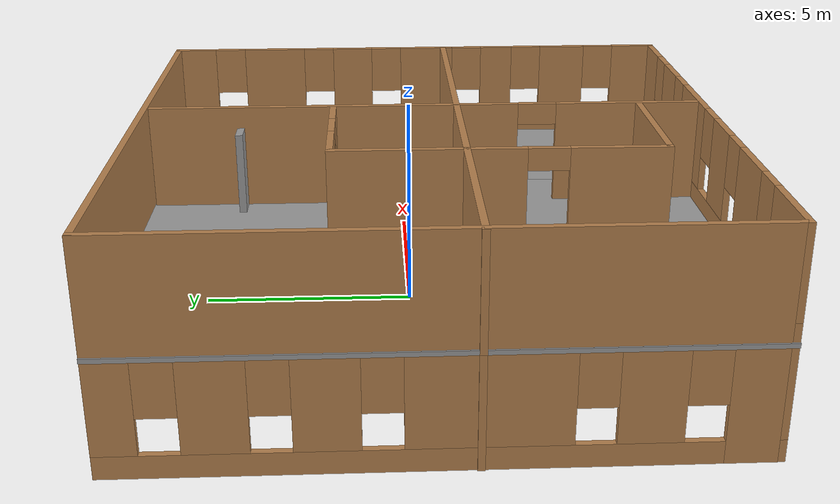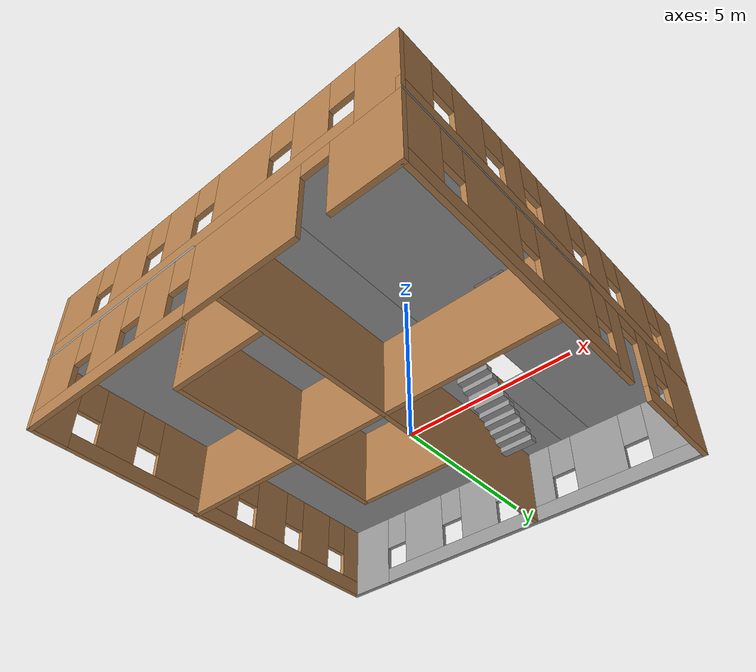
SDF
<?xml version='1.0'?>
<sdf version='1.7'>
  <model name='My_House'>
    <pose>-1.02269 -0.39336 0 0 -0 0</pose>
    <link name='Door_11'>
      <collision name='Door_11_Collision'>
        <geometry>
          <box>
            <size>0.9 0.17 2</size>
          </box>
        </geometry>
        <pose>0 0 1 0 -0 0</pose>
      </collision>
      <visual name='Door_11_Visual'>
        <pose>0 0 1 0 -0 0</pose>
        <geometry>
          <box>
            <size>0.9 0.17 2</size>
          </box>
        </geometry>
        <material>
          <script>
            <uri>file://media/materials/scripts/gazebo.material</uri>
            <name>Gazebo/Grey</name>
          </script>
        </material>
      </visual>
      <pose>-4.2238 -0.812915 2.5 0 -0 0</pose>
    </link>
    <link name='Door_13'>
      <collision name='Door_13_Collision'>
        <geometry>
          <box>
            <size>0.9 0.17 2</size>
          </box>
        </geometry>
        <pose>0 0 1 0 -0 0</pose>
      </collision>
      <visual name='Door_13_Visual'>
        <pose>0 0 1 0 -0 0</pose>
        <geometry>
          <box>
            <size>0.9 0.17 2</size>
          </box>
        </geometry>
        <material>
          <script>
            <uri>file://media/materials/scripts/gazebo.material</uri>
            <name>Gazebo/Grey</name>
          </script>
        </material>
      </visual>
      <pose>0.873598 4.32494 2.5 0 -0 0</pose>
    </link>
    <link name='Door_8'>
      <collision name='Door_8_Collision'>
        <geometry>
          <box>
            <size>0.9 0.17 2</size>
          </box>
        </geometry>
        <pose>0 0 1 0 -0 0</pose>
      </collision>
      <visual name='Door_8_Visual'>
        <pose>0 0 1 0 -0 0</pose>
        <geometry>
          <box>
            <size>0.9 0.17 2</size>
          </box>
        </geometry>
        <material>
          <script>
            <uri>file://media/materials/scripts/gazebo.material</uri>
            <name>Gazebo/Grey</name>
          </script>
        </material>
      </visual>
      <pose>4.75733 -0.812915 2.5 0 -0 0</pose>
    </link>
    <link name='Floor_6'>
      <pose>-0 0 2.5 0 -0 0</pose>
      <visual name='Floor_6_Visual_0'>
        <pose>-2.14465 0 0.05 0 -0 0</pose>
        <geometry>
          <box>
            <size>9.00115 13.25 0.1</size>
          </box>
        </geometry>
        <material>
          <script>
            <uri>file://media/materials/scripts/gazebo.material</uri>
            <name>Gazebo/Grey</name>
          </script>
          <ambient>1 1 1 1</ambient>
        </material>
        <meta>
          <layer>1</layer>
        </meta>
      </visual>
      <collision name='Floor_6_Collision_0'>
        <geometry>
          <box>
            <size>9.00115 13.25 0.1</size>
          </box>
        </geometry>
        <pose>-2.14465 0 0.05 0 -0 0</pose>
      </collision>
      <visual name='Floor_6_Visual_1'>
        <pose>4.50058 -3.58257 0.05 0 -0 0</pose>
        <geometry>
          <box>
            <size>4.28931 6.08486 0.1</size>
          </box>
        </geometry>
        <material>
          <script>
            <uri>file://media/materials/scripts/gazebo.material</uri>
            <name>Gazebo/Grey</name>
          </script>
          <ambient>1 1 1 1</ambient>
        </material>
        <meta>
          <layer>1</layer>
        </meta>
      </visual>
      <collision name='Floor_6_Collision_1'>
        <geometry>
          <box>
            <size>4.28931 6.08486 0.1</size>
          </box>
        </geometry>
        <pose>4.50058 -3.58257 0.05 0 -0 0</pose>
      </collision>
      <visual name='Floor_6_Visual_2'>
        <pose>5.00058 3.04243 0.05 0 -0 0</pose>
        <geometry>
          <box>
            <size>3.28931 7.16514 0.1</size>
          </box>
        </geometry>
        <material>
          <script>
            <uri>file://media/materials/scripts/gazebo.material</uri>
            <name>Gazebo/Grey</name>
          </script>
          <ambient>1 1 1 1</ambient>
        </material>
        <meta>
          <layer>1</layer>
        </meta>
      </visual>
      <collision name='Floor_6_Collision_2'>
        <geometry>
          <box>
            <size>3.28931 7.16514 0.1</size>
          </box>
        </geometry>
        <pose>5.00058 3.04243 0.05 0 -0 0</pose>
      </collision>
      <visual name='Floor_6_Visual_3'>
        <pose>2.85592 4.79243 0.05 0 -0 0</pose>
        <geometry>
          <box>
            <size>1 3.66514 0.1</size>
          </box>
        </geometry>
        <material>
          <script>
            <uri>file://media/materials/scripts/gazebo.material</uri>
            <name>Gazebo/Grey</name>
          </script>
          <ambient>1 1 1 1</ambient>
        </material>
        <meta>
          <layer>1</layer>
        </meta>
      </visual>
      <collision name='Floor_6_Collision_3'>
        <geometry>
          <box>
            <size>1 3.66514 0.1</size>
          </box>
        </geometry>
        <pose>2.85592 4.79243 0.05 0 -0 0</pose>
      </collision>
    </link>
    <link name='Stairs_0'>
      <visual name='Stairs_0_Visual_0'>
        <pose>2.85592 2.8432 0.083333 0 -0 0</pose>
        <geometry>
          <box>
            <size>1 0.233333 0.166667</size>
          </box>
        </geometry>
        <material>
          <script>
            <uri>file://media/materials/scripts/gazebo.material</uri>
            <name>Gazebo/Grey</name>
          </script>
          <ambient>1 1 1 1</ambient>
        </material>
        <meta>
          <layer>0</layer>
        </meta>
      </visual>
      <collision name='Stairs_0_Collision_0'>
        <geometry>
          <box>
            <size>1 0.233333 0.166667</size>
          </box>
        </geometry>
        <pose>2.85592 2.8432 0.083333 0 -0 0</pose>
      </collision>
      <visual name='Stairs_0_Visual_1'>
        <pose>2.85592 2.60986 0.25 0 -0 0</pose>
        <geometry>
          <box>
            <size>1 0.233333 0.166667</size>
          </box>
        </geometry>
        <material>
          <script>
            <uri>file://media/materials/scripts/gazebo.material</uri>
            <name>Gazebo/Grey</name>
          </script>
          <ambient>1 1 1 1</ambient>
        </material>
        <meta>
          <layer>0</layer>
        </meta>
      </visual>
      <collision name='Stairs_0_Collision_1'>
        <geometry>
          <box>
            <size>1 0.233333 0.166667</size>
          </box>
        </geometry>
        <pose>2.85592 2.60986 0.25 0 -0 0</pose>
      </collision>
      <visual name='Stairs_0_Visual_2'>
        <pose>2.85592 2.37653 0.416667 0 -0 0</pose>
        <geometry>
          <box>
            <size>1 0.233333 0.166667</size>
          </box>
        </geometry>
        <material>
          <script>
            <uri>file://media/materials/scripts/gazebo.material</uri>
            <name>Gazebo/Grey</name>
          </script>
          <ambient>1 1 1 1</ambient>
        </material>
        <meta>
          <layer>0</layer>
        </meta>
      </visual>
      <collision name='Stairs_0_Collision_2'>
        <geometry>
          <box>
            <size>1 0.233333 0.166667</size>
          </box>
        </geometry>
        <pose>2.85592 2.37653 0.416667 0 -0 0</pose>
      </collision>
      <visual name='Stairs_0_Visual_3'>
        <pose>2.85592 2.1432 0.583333 0 -0 0</pose>
        <geometry>
          <box>
            <size>1 0.233333 0.166667</size>
          </box>
        </geometry>
        <material>
          <script>
            <uri>file://media/materials/scripts/gazebo.material</uri>
            <name>Gazebo/Grey</name>
          </script>
          <ambient>1 1 1 1</ambient>
        </material>
        <meta>
          <layer>0</layer>
        </meta>
      </visual>
      <collision name='Stairs_0_Collision_3'>
        <geometry>
          <box>
            <size>1 0.233333 0.166667</size>
          </box>
        </geometry>
        <pose>2.85592 2.1432 0.583333 0 -0 0</pose>
      </collision>
      <visual name='Stairs_0_Visual_4'>
        <pose>2.85592 1.90986 0.75 0 -0 0</pose>
        <geometry>
          <box>
            <size>1 0.233333 0.166667</size>
          </box>
        </geometry>
        <material>
          <script>
            <uri>file://media/materials/scripts/gazebo.material</uri>
            <name>Gazebo/Grey</name>
          </script>
          <ambient>1 1 1 1</ambient>
        </material>
        <meta>
          <layer>0</layer>
        </meta>
      </visual>
      <collision name='Stairs_0_Collision_4'>
        <geometry>
          <box>
            <size>1 0.233333 0.166667</size>
          </box>
        </geometry>
        <pose>2.85592 1.90986 0.75 0 -0 0</pose>
      </collision>
      <visual name='Stairs_0_Visual_5'>
        <pose>2.85592 1.67653 0.916667 0 -0 0</pose>
        <geometry>
          <box>
            <size>1 0.233333 0.166667</size>
          </box>
        </geometry>
        <material>
          <script>
            <uri>file://media/materials/scripts/gazebo.material</uri>
            <name>Gazebo/Grey</name>
          </script>
          <ambient>1 1 1 1</ambient>
        </material>
        <meta>
          <layer>0</layer>
        </meta>
      </visual>
      <collision name='Stairs_0_Collision_5'>
        <geometry>
          <box>
            <size>1 0.233333 0.166667</size>
          </box>
        </geometry>
        <pose>2.85592 1.67653 0.916667 0 -0 0</pose>
      </collision>
      <visual name='Stairs_0_Visual_6'>
        <pose>2.85592 1.4432 1.08333 0 -0 0</pose>
        <geometry>
          <box>
            <size>1 0.233333 0.166667</size>
          </box>
        </geometry>
        <material>
          <script>
            <uri>file://media/materials/scripts/gazebo.material</uri>
            <name>Gazebo/Grey</name>
          </script>
          <ambient>1 1 1 1</ambient>
        </material>
        <meta>
          <layer>0</layer>
        </meta>
      </visual>
      <collision name='Stairs_0_Collision_6'>
        <geometry>
          <box>
            <size>1 0.233333 0.166667</size>
          </box>
        </geometry>
        <pose>2.85592 1.4432 1.08333 0 -0 0</pose>
      </collision>
      <visual name='Stairs_0_Visual_7'>
        <pose>2.85592 1.20986 1.25 0 -0 0</pose>
        <geometry>
          <box>
            <size>1 0.233333 0.166667</size>
          </box>
        </geometry>
        <material>
          <script>
            <uri>file://media/materials/scripts/gazebo.material</uri>
            <name>Gazebo/Grey</name>
          </script>
          <ambient>1 1 1 1</ambient>
        </material>
        <meta>
          <layer>0</layer>
        </meta>
      </visual>
      <collision name='Stairs_0_Collision_7'>
        <geometry>
          <box>
            <size>1 0.233333 0.166667</size>
          </box>
        </geometry>
        <pose>2.85592 1.20986 1.25 0 -0 0</pose>
      </collision>
      <visual name='Stairs_0_Visual_8'>
        <pose>2.85592 0.976531 1.41667 0 -0 0</pose>
        <geometry>
          <box>
            <size>1 0.233333 0.166667</size>
          </box>
        </geometry>
        <material>
          <script>
            <uri>file://media/materials/scripts/gazebo.material</uri>
            <name>Gazebo/Grey</name>
          </script>
          <ambient>1 1 1 1</ambient>
        </material>
        <meta>
          <layer>0</layer>
        </meta>
      </visual>
      <collision name='Stairs_0_Collision_8'>
        <geometry>
          <box>
            <size>1 0.233333 0.166667</size>
          </box>
        </geometry>
        <pose>2.85592 0.976531 1.41667 0 -0 0</pose>
      </collision>
      <visual name='Stairs_0_Visual_9'>
        <pose>2.85592 0.743197 1.58333 0 -0 0</pose>
        <geometry>
          <box>
            <size>1 0.233333 0.166667</size>
          </box>
        </geometry>
        <material>
          <script>
            <uri>file://media/materials/scripts/gazebo.material</uri>
            <name>Gazebo/Grey</name>
          </script>
          <ambient>1 1 1 1</ambient>
        </material>
        <meta>
          <layer>0</layer>
        </meta>
      </visual>
      <collision name='Stairs_0_Collision_9'>
        <geometry>
          <box>
            <size>1 0.233333 0.166667</size>
          </box>
        </geometry>
        <pose>2.85592 0.743197 1.58333 0 -0 0</pose>
      </collision>
      <visual name='Stairs_0_Visual_10'>
        <pose>2.85592 0.509864 1.75 0 -0 0</pose>
        <geometry>
          <box>
            <size>1 0.233333 0.166667</size>
          </box>
        </geometry>
        <material>
          <script>
            <uri>file://media/materials/scripts/gazebo.material</uri>
            <name>Gazebo/Grey</name>
          </script>
          <ambient>1 1 1 1</ambient>
        </material>
        <meta>
          <layer>0</layer>
        </meta>
      </visual>
      <collision name='Stairs_0_Collision_10'>
        <geometry>
          <box>
            <size>1 0.233333 0.166667</size>
          </box>
        </geometry>
        <pose>2.85592 0.509864 1.75 0 -0 0</pose>
      </collision>
      <visual name='Stairs_0_Visual_11'>
        <pose>2.85592 0.276531 1.91667 0 -0 0</pose>
        <geometry>
          <box>
            <size>1 0.233333 0.166667</size>
          </box>
        </geometry>
        <material>
          <script>
            <uri>file://media/materials/scripts/gazebo.material</uri>
            <name>Gazebo/Grey</name>
          </script>
          <ambient>1 1 1 1</ambient>
        </material>
        <meta>
          <layer>0</layer>
        </meta>
      </visual>
      <collision name='Stairs_0_Collision_11'>
        <geometry>
          <box>
            <size>1 0.233333 0.166667</size>
          </box>
        </geometry>
        <pose>2.85592 0.276531 1.91667 0 -0 0</pose>
      </collision>
      <visual name='Stairs_0_Visual_12'>
        <pose>2.85592 0.043197 2.08333 0 -0 0</pose>
        <geometry>
          <box>
            <size>1 0.233333 0.166667</size>
          </box>
        </geometry>
        <material>
          <script>
            <uri>file://media/materials/scripts/gazebo.material</uri>
            <name>Gazebo/Grey</name>
          </script>
          <ambient>1 1 1 1</ambient>
        </material>
        <meta>
          <layer>0</layer>
        </meta>
      </visual>
      <collision name='Stairs_0_Collision_12'>
        <geometry>
          <box>
            <size>1 0.233333 0.166667</size>
          </box>
        </geometry>
        <pose>2.85592 0.043197 2.08333 0 -0 0</pose>
      </collision>
      <visual name='Stairs_0_Visual_13'>
        <pose>2.85592 -0.190136 2.25 0 -0 0</pose>
        <geometry>
          <box>
            <size>1 0.233333 0.166667</size>
          </box>
        </geometry>
        <material>
          <script>
            <uri>file://media/materials/scripts/gazebo.material</uri>
            <name>Gazebo/Grey</name>
          </script>
          <ambient>1 1 1 1</ambient>
        </material>
        <meta>
          <layer>0</layer>
        </meta>
      </visual>
      <collision name='Stairs_0_Collision_13'>
        <geometry>
          <box>
            <size>1 0.233333 0.166667</size>
          </box>
        </geometry>
        <pose>2.85592 -0.190136 2.25 0 -0 0</pose>
      </collision>
      <visual name='Stairs_0_Visual_14'>
        <pose>2.85592 -0.423469 2.41667 0 -0 0</pose>
        <geometry>
          <box>
            <size>1 0.233333 0.166667</size>
          </box>
        </geometry>
        <material>
          <script>
            <uri>file://media/materials/scripts/gazebo.material</uri>
            <name>Gazebo/Grey</name>
          </script>
          <ambient>1 1 1 1</ambient>
        </material>
        <meta>
          <layer>0</layer>
        </meta>
      </visual>
      <collision name='Stairs_0_Collision_14'>
        <geometry>
          <box>
            <size>1 0.233333 0.166667</size>
          </box>
        </geometry>
        <pose>2.85592 -0.423469 2.41667 0 -0 0</pose>
      </collision>
    </link>
    <link name='Wall_0'>
      <pose>0.020227 6.55 0 0 -0 0</pose>
      <visual name='Wall_0_Visual_0'>
        <pose>-5.81657 0 1.25 0 -0 0</pose>
        <geometry>
          <box>
            <size>1.61687 0.15 2.5</size>
          </box>
        </geometry>
        <material>
          <script>
            <uri>file://media/materials/scripts/gazebo.material</uri>
            <name>Gazebo/Grey</name>
          </script>
          <ambient>1 1 1 1</ambient>
        </material>
        <meta>
          <layer>0</layer>
        </meta>
      </visual>
      <collision name='Wall_0_Collision_0'>
        <geometry>
          <box>
            <size>1.61687 0.15 2.5</size>
          </box>
        </geometry>
        <pose>-5.81657 0 1.25 0 -0 0</pose>
      </collision>
      <visual name='Wall_0_Visual_1'>
        <pose>0.808434 0 0.25 0 -0 0</pose>
        <geometry>
          <box>
            <size>11.6331 0.15 0.5</size>
          </box>
        </geometry>
        <material>
          <script>
            <uri>file://media/materials/scripts/gazebo.material</uri>
            <name>Gazebo/Grey</name>
          </script>
          <ambient>1 1 1 1</ambient>
        </material>
        <meta>
          <layer>0</layer>
        </meta>
      </visual>
      <collision name='Wall_0_Collision_1'>
        <geometry>
          <box>
            <size>11.6331 0.15 0.5</size>
          </box>
        </geometry>
        <pose>0.808434 0 0.25 0 -0 0</pose>
      </collision>
      <visual name='Wall_0_Visual_2'>
        <pose>-3.39446 0 1.5 0 -0 0</pose>
        <geometry>
          <box>
            <size>1.62733 0.15 2</size>
          </box>
        </geometry>
        <material>
          <script>
            <uri>file://media/materials/scripts/gazebo.material</uri>
            <name>Gazebo/Grey</name>
          </script>
          <ambient>1 1 1 1</ambient>
        </material>
        <meta>
          <layer>0</layer>
        </meta>
      </visual>
      <collision name='Wall_0_Collision_2'>
        <geometry>
          <box>
            <size>1.62733 0.15 2</size>
          </box>
        </geometry>
        <pose>-3.39446 0 1.5 0 -0 0</pose>
      </collision>
      <visual name='Wall_0_Visual_3'>
        <pose>-1.06827 0 1.5 0 -0 0</pose>
        <geometry>
          <box>
            <size>1.42506 0.15 2</size>
          </box>
        </geometry>
        <material>
          <script>
            <uri>file://media/materials/scripts/gazebo.material</uri>
            <name>Gazebo/Grey</name>
          </script>
          <ambient>1 1 1 1</ambient>
        </material>
        <meta>
          <layer>0</layer>
        </meta>
      </visual>
      <collision name='Wall_0_Collision_3'>
        <geometry>
          <box>
            <size>1.42506 0.15 2</size>
          </box>
        </geometry>
        <pose>-1.06827 0 1.5 0 -0 0</pose>
      </collision>
      <visual name='Wall_0_Visual_4'>
        <pose>1.13656 0 1.5 0 -0 0</pose>
        <geometry>
          <box>
            <size>1.3846 0.15 2</size>
          </box>
        </geometry>
        <material>
          <script>
            <uri>file://media/materials/scripts/gazebo.material</uri>
            <name>Gazebo/Grey</name>
          </script>
          <ambient>1 1 1 1</ambient>
        </material>
        <meta>
          <layer>0</layer>
        </meta>
      </visual>
      <collision name='Wall_0_Collision_4'>
        <geometry>
          <box>
            <size>1.3846 0.15 2</size>
          </box>
        </geometry>
        <pose>1.13656 0 1.5 0 -0 0</pose>
      </collision>
      <visual name='Wall_0_Visual_5'>
        <pose>3.48298 0 1.5 0 -0 0</pose>
        <geometry>
          <box>
            <size>1.70825 0.15 2</size>
          </box>
        </geometry>
        <material>
          <script>
            <uri>file://media/materials/scripts/gazebo.material</uri>
            <name>Gazebo/Grey</name>
          </script>
          <ambient>1 1 1 1</ambient>
        </material>
        <meta>
          <layer>0</layer>
        </meta>
      </visual>
      <collision name='Wall_0_Collision_5'>
        <geometry>
          <box>
            <size>1.70825 0.15 2</size>
          </box>
        </geometry>
        <pose>3.48298 0 1.5 0 -0 0</pose>
      </collision>
      <visual name='Wall_0_Visual_6'>
        <pose>5.88105 0 1.5 0 -0 0</pose>
        <geometry>
          <box>
            <size>1.48789 0.15 2</size>
          </box>
        </geometry>
        <material>
          <script>
            <uri>file://media/materials/scripts/gazebo.material</uri>
            <name>Gazebo/Grey</name>
          </script>
          <ambient>1 1 1 1</ambient>
        </material>
        <meta>
          <layer>0</layer>
        </meta>
      </visual>
      <collision name='Wall_0_Collision_6'>
        <geometry>
          <box>
            <size>1.48789 0.15 2</size>
          </box>
        </geometry>
        <pose>5.88105 0 1.5 0 -0 0</pose>
      </collision>
      <visual name='Wall_0_Visual_7'>
        <pose>-4.60813 0 1.9 0 -0 0</pose>
        <geometry>
          <box>
            <size>0.8 0.15 1.2</size>
          </box>
        </geometry>
        <material>
          <script>
            <uri>file://media/materials/scripts/gazebo.material</uri>
            <name>Gazebo/Grey</name>
          </script>
          <ambient>1 1 1 1</ambient>
        </material>
        <meta>
          <layer>0</layer>
        </meta>
      </visual>
      <collision name='Wall_0_Collision_7'>
        <geometry>
          <box>
            <size>0.8 0.15 1.2</size>
          </box>
        </geometry>
        <pose>-4.60813 0 1.9 0 -0 0</pose>
      </collision>
      <visual name='Wall_0_Visual_8'>
        <pose>-2.1808 0 1.9 0 -0 0</pose>
        <geometry>
          <box>
            <size>0.8 0.15 1.2</size>
          </box>
        </geometry>
        <material>
          <script>
            <uri>file://media/materials/scripts/gazebo.material</uri>
            <name>Gazebo/Grey</name>
          </script>
          <ambient>1 1 1 1</ambient>
        </material>
        <meta>
          <layer>0</layer>
        </meta>
      </visual>
      <collision name='Wall_0_Collision_8'>
        <geometry>
          <box>
            <size>0.8 0.15 1.2</size>
          </box>
        </geometry>
        <pose>-2.1808 0 1.9 0 -0 0</pose>
      </collision>
      <visual name='Wall_0_Visual_9'>
        <pose>0.044259 0 1.9 0 -0 0</pose>
        <geometry>
          <box>
            <size>0.8 0.15 1.2</size>
          </box>
        </geometry>
        <material>
          <script>
            <uri>file://media/materials/scripts/gazebo.material</uri>
            <name>Gazebo/Grey</name>
          </script>
          <ambient>1 1 1 1</ambient>
        </material>
        <meta>
          <layer>0</layer>
        </meta>
      </visual>
      <collision name='Wall_0_Collision_9'>
        <geometry>
          <box>
            <size>0.8 0.15 1.2</size>
          </box>
        </geometry>
        <pose>0.044259 0 1.9 0 -0 0</pose>
      </collision>
      <visual name='Wall_0_Visual_10'>
        <pose>2.22886 0 1.9 0 -0 0</pose>
        <geometry>
          <box>
            <size>0.8 0.15 1.2</size>
          </box>
        </geometry>
        <material>
          <script>
            <uri>file://media/materials/scripts/gazebo.material</uri>
            <name>Gazebo/Grey</name>
          </script>
          <ambient>1 1 1 1</ambient>
        </material>
        <meta>
          <layer>0</layer>
        </meta>
      </visual>
      <collision name='Wall_0_Collision_10'>
        <geometry>
          <box>
            <size>0.8 0.15 1.2</size>
          </box>
        </geometry>
        <pose>2.22886 0 1.9 0 -0 0</pose>
      </collision>
      <visual name='Wall_0_Visual_11'>
        <pose>4.73711 0 1.9 0 -0 0</pose>
        <geometry>
          <box>
            <size>0.8 0.15 1.2</size>
          </box>
        </geometry>
        <material>
          <script>
            <uri>file://media/materials/scripts/gazebo.material</uri>
            <name>Gazebo/Grey</name>
          </script>
          <ambient>1 1 1 1</ambient>
        </material>
        <meta>
          <layer>0</layer>
        </meta>
      </visual>
      <collision name='Wall_0_Collision_11'>
        <geometry>
          <box>
            <size>0.8 0.15 1.2</size>
          </box>
        </geometry>
        <pose>4.73711 0 1.9 0 -0 0</pose>
      </collision>
    </link>
    <link name='Wall_1'>
      <pose>6.57023 0 0 0 -0 -1.5708</pose>
      <visual name='Wall_1_Visual_0'>
        <pose>-5.71543 0 1.25 0 -0 0</pose>
        <geometry>
          <box>
            <size>1.81915 0.15 2.5</size>
          </box>
        </geometry>
        <material>
          <script>
            <uri>file://media/materials/scripts/gazebo.material</uri>
            <name>Gazebo/Wood</name>
          </script>
          <ambient>1 1 1 1</ambient>
        </material>
        <meta>
          <layer>0</layer>
        </meta>
      </visual>
      <collision name='Wall_1_Collision_0'>
        <geometry>
          <box>
            <size>1.81915 0.15 2.5</size>
          </box>
        </geometry>
        <pose>-5.71543 0 1.25 0 -0 0</pose>
      </collision>
      <visual name='Wall_1_Visual_1'>
        <pose>-2.11534 0 1.25 0 -0 0</pose>
        <geometry>
          <box>
            <size>0.687312 0.15 2.5</size>
          </box>
        </geometry>
        <material>
          <script>
            <uri>file://media/materials/scripts/gazebo.material</uri>
            <name>Gazebo/Wood</name>
          </script>
          <ambient>1 1 1 1</ambient>
        </material>
        <meta>
          <layer>0</layer>
        </meta>
      </visual>
      <collision name='Wall_1_Collision_1'>
        <geometry>
          <box>
            <size>0.687312 0.15 2.5</size>
          </box>
        </geometry>
        <pose>-2.11534 0 1.25 0 -0 0</pose>
      </collision>
      <visual name='Wall_1_Visual_2'>
        <pose>-4.08243 0 0.25 0 -0 0</pose>
        <geometry>
          <box>
            <size>1.44686 0.15 0.5</size>
          </box>
        </geometry>
        <material>
          <script>
            <uri>file://media/materials/scripts/gazebo.material</uri>
            <name>Gazebo/Wood</name>
          </script>
          <ambient>1 1 1 1</ambient>
        </material>
        <meta>
          <layer>0</layer>
        </meta>
      </visual>
      <collision name='Wall_1_Collision_2'>
        <geometry>
          <box>
            <size>1.44686 0.15 0.5</size>
          </box>
        </geometry>
        <pose>-4.08243 0 0.25 0 -0 0</pose>
      </collision>
      <visual name='Wall_1_Visual_3'>
        <pose>2.42666 0 0.25 0 -0 0</pose>
        <geometry>
          <box>
            <size>8.39669 0.15 0.5</size>
          </box>
        </geometry>
        <material>
          <script>
            <uri>file://media/materials/scripts/gazebo.material</uri>
            <name>Gazebo/Wood</name>
          </script>
          <ambient>1 1 1 1</ambient>
        </material>
        <meta>
          <layer>0</layer>
        </meta>
      </visual>
      <collision name='Wall_1_Collision_3'>
        <geometry>
          <box>
            <size>8.39669 0.15 0.5</size>
          </box>
        </geometry>
        <pose>2.42666 0 0.25 0 -0 0</pose>
      </collision>
      <visual name='Wall_1_Visual_4'>
        <pose>-3.68243 0 1.5 0 -0 0</pose>
        <geometry>
          <box>
            <size>0.646856 0.15 2</size>
          </box>
        </geometry>
        <material>
          <script>
            <uri>file://media/materials/scripts/gazebo.material</uri>
            <name>Gazebo/Wood</name>
          </script>
          <ambient>1 1 1 1</ambient>
        </material>
        <meta>
          <layer>0</layer>
        </meta>
      </visual>
      <collision name='Wall_1_Collision_4'>
        <geometry>
          <box>
            <size>0.646856 0.15 2</size>
          </box>
        </geometry>
        <pose>-3.68243 0 1.5 0 -0 0</pose>
      </collision>
      <visual name='Wall_1_Visual_5'>
        <pose>-3.68243 0 1.5 0 -0 0</pose>
        <geometry>
          <box>
            <size>0.646856 0.15 2</size>
          </box>
        </geometry>
        <material>
          <script>
            <uri>file://media/materials/scripts/gazebo.material</uri>
            <name>Gazebo/Wood</name>
          </script>
          <ambient>1 1 1 1</ambient>
        </material>
        <meta>
          <layer>0</layer>
        </meta>
      </visual>
      <collision name='Wall_1_Collision_5'>
        <geometry>
          <box>
            <size>0.646856 0.15 2</size>
          </box>
        </geometry>
        <pose>-3.68243 0 1.5 0 -0 0</pose>
      </collision>
      <visual name='Wall_1_Visual_6'>
        <pose>0.30722 0 1.5 0 -0 0</pose>
        <geometry>
          <box>
            <size>2.55781 0.15 2</size>
          </box>
        </geometry>
        <material>
          <script>
            <uri>file://media/materials/scripts/gazebo.material</uri>
            <name>Gazebo/Wood</name>
          </script>
          <ambient>1 1 1 1</ambient>
        </material>
        <meta>
          <layer>0</layer>
        </meta>
      </visual>
      <collision name='Wall_1_Collision_6'>
        <geometry>
          <box>
            <size>2.55781 0.15 2</size>
          </box>
        </geometry>
        <pose>0.30722 0 1.5 0 -0 0</pose>
      </collision>
      <visual name='Wall_1_Visual_7'>
        <pose>3.44253 0 1.5 0 -0 0</pose>
        <geometry>
          <box>
            <size>2.1128 0.15 2</size>
          </box>
        </geometry>
        <material>
          <script>
            <uri>file://media/materials/scripts/gazebo.material</uri>
            <name>Gazebo/Wood</name>
          </script>
          <ambient>1 1 1 1</ambient>
        </material>
        <meta>
          <layer>0</layer>
        </meta>
      </visual>
      <collision name='Wall_1_Collision_7'>
        <geometry>
          <box>
            <size>2.1128 0.15 2</size>
          </box>
        </geometry>
        <pose>3.44253 0 1.5 0 -0 0</pose>
      </collision>
      <visual name='Wall_1_Visual_8'>
        <pose>5.96196 0 1.5 0 -0 0</pose>
        <geometry>
          <box>
            <size>1.32607 0.15 2</size>
          </box>
        </geometry>
        <material>
          <script>
            <uri>file://media/materials/scripts/gazebo.material</uri>
            <name>Gazebo/Wood</name>
          </script>
          <ambient>1 1 1 1</ambient>
        </material>
        <meta>
          <layer>0</layer>
        </meta>
      </visual>
      <collision name='Wall_1_Collision_8'>
        <geometry>
          <box>
            <size>1.32607 0.15 2</size>
          </box>
        </geometry>
        <pose>5.96196 0 1.5 0 -0 0</pose>
      </collision>
      <visual name='Wall_1_Visual_9'>
        <pose>-4.40585 0 1.9 0 -0 0</pose>
        <geometry>
          <box>
            <size>0.8 0.15 1.2</size>
          </box>
        </geometry>
        <material>
          <script>
            <uri>file://media/materials/scripts/gazebo.material</uri>
            <name>Gazebo/Wood</name>
          </script>
          <ambient>1 1 1 1</ambient>
        </material>
        <meta>
          <layer>0</layer>
        </meta>
      </visual>
      <collision name='Wall_1_Collision_9'>
        <geometry>
          <box>
            <size>0.8 0.15 1.2</size>
          </box>
        </geometry>
        <pose>-4.40585 0 1.9 0 -0 0</pose>
      </collision>
      <visual name='Wall_1_Visual_10'>
        <pose>-1.37169 0 1.9 0 -0 0</pose>
        <geometry>
          <box>
            <size>0.8 0.15 1.2</size>
          </box>
        </geometry>
        <material>
          <script>
            <uri>file://media/materials/scripts/gazebo.material</uri>
            <name>Gazebo/Wood</name>
          </script>
          <ambient>1 1 1 1</ambient>
        </material>
        <meta>
          <layer>0</layer>
        </meta>
      </visual>
      <collision name='Wall_1_Collision_10'>
        <geometry>
          <box>
            <size>0.8 0.15 1.2</size>
          </box>
        </geometry>
        <pose>-1.37169 0 1.9 0 -0 0</pose>
      </collision>
      <visual name='Wall_1_Visual_11'>
        <pose>1.98613 0 1.9 0 -0 0</pose>
        <geometry>
          <box>
            <size>0.8 0.15 1.2</size>
          </box>
        </geometry>
        <material>
          <script>
            <uri>file://media/materials/scripts/gazebo.material</uri>
            <name>Gazebo/Wood</name>
          </script>
          <ambient>1 1 1 1</ambient>
        </material>
        <meta>
          <layer>0</layer>
        </meta>
      </visual>
      <collision name='Wall_1_Collision_11'>
        <geometry>
          <box>
            <size>0.8 0.15 1.2</size>
          </box>
        </geometry>
        <pose>1.98613 0 1.9 0 -0 0</pose>
      </collision>
      <visual name='Wall_1_Visual_12'>
        <pose>4.89893 0 1.9 0 -0 0</pose>
        <geometry>
          <box>
            <size>0.8 0.15 1.2</size>
          </box>
        </geometry>
        <material>
          <script>
            <uri>file://media/materials/scripts/gazebo.material</uri>
            <name>Gazebo/Wood</name>
          </script>
          <ambient>1 1 1 1</ambient>
        </material>
        <meta>
          <layer>0</layer>
        </meta>
      </visual>
      <collision name='Wall_1_Collision_12'>
        <geometry>
          <box>
            <size>0.8 0.15 1.2</size>
          </box>
        </geometry>
        <pose>4.89893 0 1.9 0 -0 0</pose>
      </collision>
      <visual name='Wall_1_Visual_13'>
        <pose>-2.909 0 2.25 0 -0 0</pose>
        <geometry>
          <box>
            <size>0.9 0.15 0.5</size>
          </box>
        </geometry>
        <material>
          <script>
            <uri>file://media/materials/scripts/gazebo.material</uri>
            <name>Gazebo/Wood</name>
          </script>
          <ambient>1 1 1 1</ambient>
        </material>
        <meta>
          <layer>0</layer>
        </meta>
      </visual>
      <collision name='Wall_1_Collision_13'>
        <geometry>
          <box>
            <size>0.9 0.15 0.5</size>
          </box>
        </geometry>
        <pose>-2.909 0 2.25 0 -0 0</pose>
      </collision>
      <visual name='Wall_1_Visual_14'>
        <pose>-2.909 0 2.25 0 -0 0</pose>
        <geometry>
          <box>
            <size>0.9 0.15 0.5</size>
          </box>
        </geometry>
        <material>
          <script>
            <uri>file://media/materials/scripts/gazebo.material</uri>
            <name>Gazebo/Wood</name>
          </script>
          <ambient>1 1 1 1</ambient>
        </material>
        <meta>
          <layer>0</layer>
        </meta>
      </visual>
      <collision name='Wall_1_Collision_14'>
        <geometry>
          <box>
            <size>0.9 0.15 0.5</size>
          </box>
        </geometry>
        <pose>-2.909 0 2.25 0 -0 0</pose>
      </collision>
    </link>
    <link name='Wall_10'>
      <collision name='Wall_10_Collision'>
        <geometry>
          <box>
            <size>3.25 0.15 2.5</size>
          </box>
        </geometry>
        <pose>0 0 1.25 0 -0 0</pose>
      </collision>
      <visual name='Wall_10_Visual'>
        <pose>0 0 1.25 0 -0 0</pose>
        <geometry>
          <box>
            <size>3.25 0.15 2.5</size>
          </box>
        </geometry>
        <material>
          <script>
            <uri>file://media/materials/scripts/gazebo.material</uri>
            <name>Gazebo/Wood</name>
          </script>
          <ambient>1 1 1 1</ambient>
        </material>
        <meta>
          <layer>0</layer>
        </meta>
      </visual>
      <pose>-0.651026 2.15845 0 0 -0 0</pose>
    </link>
    <link name='Wall_12'>
      <collision name='Wall_12_Collision'>
        <geometry>
          <box>
            <size>4.5 0.15 2.5</size>
          </box>
        </geometry>
        <pose>0 0 1.25 0 -0 0</pose>
      </collision>
      <visual name='Wall_12_Visual'>
        <pose>0 0 1.25 0 -0 0</pose>
        <geometry>
          <box>
            <size>4.5 0.15 2.5</size>
          </box>
        </geometry>
        <material>
          <script>
            <uri>file://media/materials/scripts/gazebo.material</uri>
            <name>Gazebo/Wood</name>
          </script>
          <ambient>1 1 1 1</ambient>
        </material>
        <meta>
          <layer>0</layer>
        </meta>
      </visual>
      <pose>-2.20103 -2.86655 0 0 -0 -1.5708</pose>
    </link>
    <link name='Wall_13'>
      <collision name='Wall_13_Collision'>
        <geometry>
          <box>
            <size>3.25 0.15 2.5</size>
          </box>
        </geometry>
        <pose>0 0 1.25 0 -0 0</pose>
      </collision>
      <visual name='Wall_13_Visual'>
        <pose>0 0 1.25 0 -0 0</pose>
        <geometry>
          <box>
            <size>3.25 0.15 2.5</size>
          </box>
        </geometry>
        <material>
          <script>
            <uri>file://media/materials/scripts/gazebo.material</uri>
            <name>Gazebo/Wood</name>
          </script>
          <ambient>1 1 1 1</ambient>
        </material>
        <meta>
          <layer>0</layer>
        </meta>
      </visual>
      <pose>-0.651026 -5.04155 0 0 -0 0</pose>
    </link>
    <link name='Wall_2'>
      <pose>0.020227 -6.55 0 0 -0 3.14159</pose>
      <visual name='Wall_2_Visual_0'>
        <pose>-5.58241 0 1.25 0 -0 0</pose>
        <geometry>
          <box>
            <size>2.08518 0.15 2.5</size>
          </box>
        </geometry>
        <material>
          <script>
            <uri>file://media/materials/scripts/gazebo.material</uri>
            <name>Gazebo/Wood</name>
          </script>
          <ambient>1 0.764706 0.305882 1</ambient>
        </material>
        <meta>
          <layer>0</layer>
        </meta>
      </visual>
      <collision name='Wall_2_Collision_0'>
        <geometry>
          <box>
            <size>2.08518 0.15 2.5</size>
          </box>
        </geometry>
        <pose>-5.58241 0 1.25 0 -0 0</pose>
      </collision>
      <visual name='Wall_2_Visual_1'>
        <pose>-1.77908 0 1.25 0 -0 0</pose>
        <geometry>
          <box>
            <size>3.72148 0.15 2.5</size>
          </box>
        </geometry>
        <material>
          <script>
            <uri>file://media/materials/scripts/gazebo.material</uri>
            <name>Gazebo/Wood</name>
          </script>
          <ambient>1 0.764706 0.305882 1</ambient>
        </material>
        <meta>
          <layer>0</layer>
        </meta>
      </visual>
      <collision name='Wall_2_Collision_1'>
        <geometry>
          <box>
            <size>3.72148 0.15 2.5</size>
          </box>
        </geometry>
        <pose>-1.77908 0 1.25 0 -0 0</pose>
      </collision>
      <visual name='Wall_2_Visual_2'>
        <pose>3.35333 0 0.25 0 -0 0</pose>
        <geometry>
          <box>
            <size>6.54334 0.15 0.5</size>
          </box>
        </geometry>
        <material>
          <script>
            <uri>file://media/materials/scripts/gazebo.material</uri>
            <name>Gazebo/Wood</name>
          </script>
          <ambient>1 0.764706 0.305882 1</ambient>
        </material>
        <meta>
          <layer>0</layer>
        </meta>
      </visual>
      <collision name='Wall_2_Collision_2'>
        <geometry>
          <box>
            <size>6.54334 0.15 0.5</size>
          </box>
        </geometry>
        <pose>3.35333 0 0.25 0 -0 0</pose>
      </collision>
      <visual name='Wall_2_Visual_3'>
        <pose>1.4526 0 1.5 0 -0 0</pose>
        <geometry>
          <box>
            <size>1.14187 0.15 2</size>
          </box>
        </geometry>
        <material>
          <script>
            <uri>file://media/materials/scripts/gazebo.material</uri>
            <name>Gazebo/Wood</name>
          </script>
          <ambient>1 0.764706 0.305882 1</ambient>
        </material>
        <meta>
          <layer>0</layer>
        </meta>
      </visual>
      <collision name='Wall_2_Collision_3'>
        <geometry>
          <box>
            <size>1.14187 0.15 2</size>
          </box>
        </geometry>
        <pose>1.4526 0 1.5 0 -0 0</pose>
      </collision>
      <visual name='Wall_2_Visual_4'>
        <pose>3.45515 0 1.5 0 -0 0</pose>
        <geometry>
          <box>
            <size>1.26323 0.15 2</size>
          </box>
        </geometry>
        <material>
          <script>
            <uri>file://media/materials/scripts/gazebo.material</uri>
            <name>Gazebo/Wood</name>
          </script>
          <ambient>1 0.764706 0.305882 1</ambient>
        </material>
        <meta>
          <layer>0</layer>
        </meta>
      </visual>
      <collision name='Wall_2_Collision_4'>
        <geometry>
          <box>
            <size>1.26323 0.15 2</size>
          </box>
        </geometry>
        <pose>3.45515 0 1.5 0 -0 0</pose>
      </collision>
      <visual name='Wall_2_Visual_5'>
        <pose>5.75588 0 1.5 0 -0 0</pose>
        <geometry>
          <box>
            <size>1.73823 0.15 2</size>
          </box>
        </geometry>
        <material>
          <script>
            <uri>file://media/materials/scripts/gazebo.material</uri>
            <name>Gazebo/Wood</name>
          </script>
          <ambient>1 0.764706 0.305882 1</ambient>
        </material>
        <meta>
          <layer>0</layer>
        </meta>
      </visual>
      <collision name='Wall_2_Collision_5'>
        <geometry>
          <box>
            <size>1.73823 0.15 2</size>
          </box>
        </geometry>
        <pose>5.75588 0 1.5 0 -0 0</pose>
      </collision>
      <visual name='Wall_2_Visual_6'>
        <pose>0.481663 0 1.9 0 -0 0</pose>
        <geometry>
          <box>
            <size>0.8 0.15 1.2</size>
          </box>
        </geometry>
        <material>
          <script>
            <uri>file://media/materials/scripts/gazebo.material</uri>
            <name>Gazebo/Wood</name>
          </script>
          <ambient>1 0.764706 0.305882 1</ambient>
        </material>
        <meta>
          <layer>0</layer>
        </meta>
      </visual>
      <collision name='Wall_2_Collision_6'>
        <geometry>
          <box>
            <size>0.8 0.15 1.2</size>
          </box>
        </geometry>
        <pose>0.481663 0 1.9 0 -0 0</pose>
      </collision>
      <visual name='Wall_2_Visual_7'>
        <pose>2.42353 0 1.9 0 -0 0</pose>
        <geometry>
          <box>
            <size>0.8 0.15 1.2</size>
          </box>
        </geometry>
        <material>
          <script>
            <uri>file://media/materials/scripts/gazebo.material</uri>
            <name>Gazebo/Wood</name>
          </script>
          <ambient>1 0.764706 0.305882 1</ambient>
        </material>
        <meta>
          <layer>0</layer>
        </meta>
      </visual>
      <collision name='Wall_2_Collision_7'>
        <geometry>
          <box>
            <size>0.8 0.15 1.2</size>
          </box>
        </geometry>
        <pose>2.42353 0 1.9 0 -0 0</pose>
      </collision>
      <visual name='Wall_2_Visual_8'>
        <pose>4.48677 0 1.9 0 -0 0</pose>
        <geometry>
          <box>
            <size>0.8 0.15 1.2</size>
          </box>
        </geometry>
        <material>
          <script>
            <uri>file://media/materials/scripts/gazebo.material</uri>
            <name>Gazebo/Wood</name>
          </script>
          <ambient>1 0.764706 0.305882 1</ambient>
        </material>
        <meta>
          <layer>0</layer>
        </meta>
      </visual>
      <collision name='Wall_2_Collision_8'>
        <geometry>
          <box>
            <size>0.8 0.15 1.2</size>
          </box>
        </geometry>
        <pose>4.48677 0 1.9 0 -0 0</pose>
      </collision>
      <visual name='Wall_2_Visual_9'>
        <pose>-4.08982 0 2.25 0 -0 0</pose>
        <geometry>
          <box>
            <size>0.9 0.15 0.5</size>
          </box>
        </geometry>
        <material>
          <script>
            <uri>file://media/materials/scripts/gazebo.material</uri>
            <name>Gazebo/Wood</name>
          </script>
          <ambient>1 0.764706 0.305882 1</ambient>
        </material>
        <meta>
          <layer>0</layer>
        </meta>
      </visual>
      <collision name='Wall_2_Collision_9'>
        <geometry>
          <box>
            <size>0.9 0.15 0.5</size>
          </box>
        </geometry>
        <pose>-4.08982 0 2.25 0 -0 0</pose>
      </collision>
    </link>
    <link name='Wall_3'>
      <pose>-6.52977 0 0 0 -0 1.5708</pose>
      <visual name='Wall_3_Visual_0'>
        <pose>-6.02265 0 1.25 0 -0 0</pose>
        <geometry>
          <box>
            <size>1.2047 0.15 2.5</size>
          </box>
        </geometry>
        <material>
          <script>
            <uri>file://media/materials/scripts/gazebo.material</uri>
            <name>Gazebo/Wood</name>
          </script>
          <ambient>1 1 1 1</ambient>
        </material>
        <meta>
          <layer>0</layer>
        </meta>
      </visual>
      <collision name='Wall_3_Collision_0'>
        <geometry>
          <box>
            <size>1.2047 0.15 2.5</size>
          </box>
        </geometry>
        <pose>-6.02265 0 1.25 0 -0 0</pose>
      </collision>
      <visual name='Wall_3_Visual_1'>
        <pose>0.602352 0 0.25 0 -0 0</pose>
        <geometry>
          <box>
            <size>12.0453 0.15 0.5</size>
          </box>
        </geometry>
        <material>
          <script>
            <uri>file://media/materials/scripts/gazebo.material</uri>
            <name>Gazebo/Wood</name>
          </script>
          <ambient>1 1 1 1</ambient>
        </material>
        <meta>
          <layer>0</layer>
        </meta>
      </visual>
      <collision name='Wall_3_Collision_1'>
        <geometry>
          <box>
            <size>12.0453 0.15 0.5</size>
          </box>
        </geometry>
        <pose>0.602352 0 0.25 0 -0 0</pose>
      </collision>
      <visual name='Wall_3_Visual_2'>
        <pose>-3.96845 0 1.5 0 -0 0</pose>
        <geometry>
          <box>
            <size>1.30369 0.15 2</size>
          </box>
        </geometry>
        <material>
          <script>
            <uri>file://media/materials/scripts/gazebo.material</uri>
            <name>Gazebo/Wood</name>
          </script>
          <ambient>1 1 1 1</ambient>
        </material>
        <meta>
          <layer>0</layer>
        </meta>
      </visual>
      <collision name='Wall_3_Collision_2'>
        <geometry>
          <box>
            <size>1.30369 0.15 2</size>
          </box>
        </geometry>
        <pose>-3.96845 0 1.5 0 -0 0</pose>
      </collision>
      <visual name='Wall_3_Visual_3'>
        <pose>-0.893826 0 1.5 0 -0 0</pose>
        <geometry>
          <box>
            <size>3.24556 0.15 2</size>
          </box>
        </geometry>
        <material>
          <script>
            <uri>file://media/materials/scripts/gazebo.material</uri>
            <name>Gazebo/Wood</name>
          </script>
          <ambient>1 1 1 1</ambient>
        </material>
        <meta>
          <layer>0</layer>
        </meta>
      </visual>
      <collision name='Wall_3_Collision_3'>
        <geometry>
          <box>
            <size>3.24556 0.15 2</size>
          </box>
        </geometry>
        <pose>-0.893826 0 1.5 0 -0 0</pose>
      </collision>
      <visual name='Wall_3_Visual_4'>
        <pose>2.1808 0 1.5 0 -0 0</pose>
        <geometry>
          <box>
            <size>1.30369 0.15 2</size>
          </box>
        </geometry>
        <material>
          <script>
            <uri>file://media/materials/scripts/gazebo.material</uri>
            <name>Gazebo/Wood</name>
          </script>
          <ambient>1 1 1 1</ambient>
        </material>
        <meta>
          <layer>0</layer>
        </meta>
      </visual>
      <collision name='Wall_3_Collision_4'>
        <geometry>
          <box>
            <size>1.30369 0.15 2</size>
          </box>
        </geometry>
        <pose>2.1808 0 1.5 0 -0 0</pose>
      </collision>
      <visual name='Wall_3_Visual_5'>
        <pose>4.28449 0 1.5 0 -0 0</pose>
        <geometry>
          <box>
            <size>1.30369 0.15 2</size>
          </box>
        </geometry>
        <material>
          <script>
            <uri>file://media/materials/scripts/gazebo.material</uri>
            <name>Gazebo/Wood</name>
          </script>
          <ambient>1 1 1 1</ambient>
        </material>
        <meta>
          <layer>0</layer>
        </meta>
      </visual>
      <collision name='Wall_3_Collision_5'>
        <geometry>
          <box>
            <size>1.30369 0.15 2</size>
          </box>
        </geometry>
        <pose>4.28449 0 1.5 0 -0 0</pose>
      </collision>
      <visual name='Wall_3_Visual_6'>
        <pose>6.18067 0 1.5 0 -0 0</pose>
        <geometry>
          <box>
            <size>0.888667 0.15 2</size>
          </box>
        </geometry>
        <material>
          <script>
            <uri>file://media/materials/scripts/gazebo.material</uri>
            <name>Gazebo/Wood</name>
          </script>
          <ambient>1 1 1 1</ambient>
        </material>
        <meta>
          <layer>0</layer>
        </meta>
      </visual>
      <collision name='Wall_3_Collision_6'>
        <geometry>
          <box>
            <size>0.888667 0.15 2</size>
          </box>
        </geometry>
        <pose>6.18067 0 1.5 0 -0 0</pose>
      </collision>
      <visual name='Wall_3_Visual_7'>
        <pose>-5.02029 0 1.9 0 -0 0</pose>
        <geometry>
          <box>
            <size>0.8 0.15 1.2</size>
          </box>
        </geometry>
        <material>
          <script>
            <uri>file://media/materials/scripts/gazebo.material</uri>
            <name>Gazebo/Wood</name>
          </script>
          <ambient>1 1 1 1</ambient>
        </material>
        <meta>
          <layer>0</layer>
        </meta>
      </visual>
      <collision name='Wall_3_Collision_7'>
        <geometry>
          <box>
            <size>0.8 0.15 1.2</size>
          </box>
        </geometry>
        <pose>-5.02029 0 1.9 0 -0 0</pose>
      </collision>
      <visual name='Wall_3_Visual_8'>
        <pose>-2.91661 0 1.9 0 -0 0</pose>
        <geometry>
          <box>
            <size>0.8 0.15 1.2</size>
          </box>
        </geometry>
        <material>
          <script>
            <uri>file://media/materials/scripts/gazebo.material</uri>
            <name>Gazebo/Wood</name>
          </script>
          <ambient>1 1 1 1</ambient>
        </material>
        <meta>
          <layer>0</layer>
        </meta>
      </visual>
      <collision name='Wall_3_Collision_8'>
        <geometry>
          <box>
            <size>0.8 0.15 1.2</size>
          </box>
        </geometry>
        <pose>-2.91661 0 1.9 0 -0 0</pose>
      </collision>
      <visual name='Wall_3_Visual_9'>
        <pose>1.12895 0 1.9 0 -0 0</pose>
        <geometry>
          <box>
            <size>0.8 0.15 1.2</size>
          </box>
        </geometry>
        <material>
          <script>
            <uri>file://media/materials/scripts/gazebo.material</uri>
            <name>Gazebo/Wood</name>
          </script>
          <ambient>1 1 1 1</ambient>
        </material>
        <meta>
          <layer>0</layer>
        </meta>
      </visual>
      <collision name='Wall_3_Collision_9'>
        <geometry>
          <box>
            <size>0.8 0.15 1.2</size>
          </box>
        </geometry>
        <pose>1.12895 0 1.9 0 -0 0</pose>
      </collision>
      <visual name='Wall_3_Visual_10'>
        <pose>3.23264 0 1.9 0 -0 0</pose>
        <geometry>
          <box>
            <size>0.8 0.15 1.2</size>
          </box>
        </geometry>
        <material>
          <script>
            <uri>file://media/materials/scripts/gazebo.material</uri>
            <name>Gazebo/Wood</name>
          </script>
          <ambient>1 1 1 1</ambient>
        </material>
        <meta>
          <layer>0</layer>
        </meta>
      </visual>
      <collision name='Wall_3_Collision_10'>
        <geometry>
          <box>
            <size>0.8 0.15 1.2</size>
          </box>
        </geometry>
        <pose>3.23264 0 1.9 0 -0 0</pose>
      </collision>
      <visual name='Wall_3_Visual_11'>
        <pose>5.33633 0 1.9 0 -0 0</pose>
        <geometry>
          <box>
            <size>0.8 0.15 1.2</size>
          </box>
        </geometry>
        <material>
          <script>
            <uri>file://media/materials/scripts/gazebo.material</uri>
            <name>Gazebo/Wood</name>
          </script>
          <ambient>1 1 1 1</ambient>
        </material>
        <meta>
          <layer>0</layer>
        </meta>
      </visual>
      <collision name='Wall_3_Collision_11'>
        <geometry>
          <box>
            <size>0.8 0.15 1.2</size>
          </box>
        </geometry>
        <pose>5.33633 0 1.9 0 -0 0</pose>
      </collision>
    </link>
    <link name='Wall_5'>
      <collision name='Wall_5_Collision'>
        <geometry>
          <box>
            <size>13.25 0.15 2.5</size>
          </box>
        </geometry>
        <pose>0 0 1.25 0 -0 0</pose>
      </collision>
      <visual name='Wall_5_Visual'>
        <pose>0 0 1.25 0 -0 0</pose>
        <geometry>
          <box>
            <size>13.25 0.15 2.5</size>
          </box>
        </geometry>
        <material>
          <script>
            <uri>file://media/materials/scripts/gazebo.material</uri>
            <name>Gazebo/Wood</name>
          </script>
          <ambient>1 1 1 1</ambient>
        </material>
        <meta>
          <layer>0</layer>
        </meta>
      </visual>
      <pose>-0.020228 -0.732004 0 0 -0 0</pose>
    </link>
    <link name='Wall_7'>
      <collision name='Wall_7_Collision'>
        <geometry>
          <box>
            <size>13 0.15 2.5</size>
          </box>
        </geometry>
        <pose>0 0 1.25 0 -0 0</pose>
      </collision>
      <visual name='Wall_7_Visual'>
        <pose>0 0 1.25 0 -0 0</pose>
        <geometry>
          <box>
            <size>13 0.15 2.5</size>
          </box>
        </geometry>
        <material>
          <script>
            <uri>file://media/materials/scripts/gazebo.material</uri>
            <name>Gazebo/Wood</name>
          </script>
          <ambient>1 1 1 1</ambient>
        </material>
        <meta>
          <layer>0</layer>
        </meta>
      </visual>
      <pose>1.03542 -0.01124 0 0 -0 1.5708</pose>
    </link>
    <link name='Wall_75'>
      <collision name='Wall_75_Collision'>
        <geometry>
          <box>
            <size>13.25 0.15 2.5</size>
          </box>
        </geometry>
        <pose>0 0 1.25 0 -0 0</pose>
      </collision>
      <visual name='Wall_75_Visual'>
        <pose>0 0 1.25 0 -0 0</pose>
        <geometry>
          <box>
            <size>13.25 0.15 2.5</size>
          </box>
        </geometry>
        <material>
          <script>
            <uri>file://media/materials/scripts/gazebo.material</uri>
            <name>Gazebo/Wood</name>
          </script>
          <ambient>1 0.764706 0.305882 1</ambient>
        </material>
        <meta>
          <layer>1</layer>
        </meta>
      </visual>
      <pose>0.020227 6.55 2.5 0 -0 0</pose>
    </link>
    <link name='Wall_76'>
      <pose>6.57023 0 2.5 0 -0 -1.5708</pose>
      <visual name='Wall_76_Visual_0'>
        <pose>-6.07953 0 1.25 0 -0 0</pose>
        <geometry>
          <box>
            <size>1.09095 0.15 2.5</size>
          </box>
        </geometry>
        <material>
          <script>
            <uri>file://media/materials/scripts/gazebo.material</uri>
            <name>Gazebo/Wood</name>
          </script>
          <ambient>1 0.764706 0.305882 1</ambient>
        </material>
        <meta>
          <layer>1</layer>
        </meta>
      </visual>
      <collision name='Wall_76_Collision_0'>
        <geometry>
          <box>
            <size>1.09095 0.15 2.5</size>
          </box>
        </geometry>
        <pose>-6.07953 0 1.25 0 -0 0</pose>
      </collision>
      <visual name='Wall_76_Visual_1'>
        <pose>0.545473 0 0.25 0 -0 0</pose>
        <geometry>
          <box>
            <size>12.1591 0.15 0.5</size>
          </box>
        </geometry>
        <material>
          <script>
            <uri>file://media/materials/scripts/gazebo.material</uri>
            <name>Gazebo/Wood</name>
          </script>
          <ambient>1 0.764706 0.305882 1</ambient>
        </material>
        <meta>
          <layer>1</layer>
        </meta>
      </visual>
      <collision name='Wall_76_Collision_1'>
        <geometry>
          <box>
            <size>12.1591 0.15 0.5</size>
          </box>
        </geometry>
        <pose>0.545473 0 0.25 0 -0 0</pose>
      </collision>
      <visual name='Wall_76_Visual_2'>
        <pose>-3.92039 0 1.5 0 -0 0</pose>
        <geometry>
          <box>
            <size>1.62733 0.15 2</size>
          </box>
        </geometry>
        <material>
          <script>
            <uri>file://media/materials/scripts/gazebo.material</uri>
            <name>Gazebo/Wood</name>
          </script>
          <ambient>1 0.764706 0.305882 1</ambient>
        </material>
        <meta>
          <layer>1</layer>
        </meta>
      </visual>
      <collision name='Wall_76_Collision_2'>
        <geometry>
          <box>
            <size>1.62733 0.15 2</size>
          </box>
        </geometry>
        <pose>-3.92039 0 1.5 0 -0 0</pose>
      </collision>
      <visual name='Wall_76_Visual_3'>
        <pose>-1.77624 0 1.5 0 -0 0</pose>
        <geometry>
          <box>
            <size>1.06096 0.15 2</size>
          </box>
        </geometry>
        <material>
          <script>
            <uri>file://media/materials/scripts/gazebo.material</uri>
            <name>Gazebo/Wood</name>
          </script>
          <ambient>1 0.764706 0.305882 1</ambient>
        </material>
        <meta>
          <layer>1</layer>
        </meta>
      </visual>
      <collision name='Wall_76_Collision_3'>
        <geometry>
          <box>
            <size>1.06096 0.15 2</size>
          </box>
        </geometry>
        <pose>-1.77624 0 1.5 0 -0 0</pose>
      </collision>
      <visual name='Wall_76_Visual_4'>
        <pose>0.266765 0 1.5 0 -0 0</pose>
        <geometry>
          <box>
            <size>1.42506 0.15 2</size>
          </box>
        </geometry>
        <material>
          <script>
            <uri>file://media/materials/scripts/gazebo.material</uri>
            <name>Gazebo/Wood</name>
          </script>
          <ambient>1 0.764706 0.305882 1</ambient>
        </material>
        <meta>
          <layer>1</layer>
        </meta>
      </visual>
      <collision name='Wall_76_Collision_4'>
        <geometry>
          <box>
            <size>1.42506 0.15 2</size>
          </box>
        </geometry>
        <pose>0.266765 0 1.5 0 -0 0</pose>
      </collision>
      <visual name='Wall_76_Visual_5'>
        <pose>2.20863 0 1.5 0 -0 0</pose>
        <geometry>
          <box>
            <size>0.858679 0.15 2</size>
          </box>
        </geometry>
        <material>
          <script>
            <uri>file://media/materials/scripts/gazebo.material</uri>
            <name>Gazebo/Wood</name>
          </script>
          <ambient>1 0.764706 0.305882 1</ambient>
        </material>
        <meta>
          <layer>1</layer>
        </meta>
      </visual>
      <collision name='Wall_76_Collision_5'>
        <geometry>
          <box>
            <size>0.858679 0.15 2</size>
          </box>
        </geometry>
        <pose>2.20863 0 1.5 0 -0 0</pose>
      </collision>
      <visual name='Wall_76_Visual_6'>
        <pose>4.04936 0 1.5 0 -0 0</pose>
        <geometry>
          <box>
            <size>1.22278 0.15 2</size>
          </box>
        </geometry>
        <material>
          <script>
            <uri>file://media/materials/scripts/gazebo.material</uri>
            <name>Gazebo/Wood</name>
          </script>
          <ambient>1 0.764706 0.305882 1</ambient>
        </material>
        <meta>
          <layer>1</layer>
        </meta>
      </visual>
      <collision name='Wall_76_Collision_6'>
        <geometry>
          <box>
            <size>1.22278 0.15 2</size>
          </box>
        </geometry>
        <pose>4.04936 0 1.5 0 -0 0</pose>
      </collision>
      <visual name='Wall_76_Visual_7'>
        <pose>6.04288 0 1.5 0 -0 0</pose>
        <geometry>
          <box>
            <size>1.16425 0.15 2</size>
          </box>
        </geometry>
        <material>
          <script>
            <uri>file://media/materials/scripts/gazebo.material</uri>
            <name>Gazebo/Wood</name>
          </script>
          <ambient>1 0.764706 0.305882 1</ambient>
        </material>
        <meta>
          <layer>1</layer>
        </meta>
      </visual>
      <collision name='Wall_76_Collision_7'>
        <geometry>
          <box>
            <size>1.16425 0.15 2</size>
          </box>
        </geometry>
        <pose>6.04288 0 1.5 0 -0 0</pose>
      </collision>
      <visual name='Wall_76_Visual_8'>
        <pose>-5.13406 0 1.9 0 -0 0</pose>
        <geometry>
          <box>
            <size>0.8 0.15 1.2</size>
          </box>
        </geometry>
        <material>
          <script>
            <uri>file://media/materials/scripts/gazebo.material</uri>
            <name>Gazebo/Wood</name>
          </script>
          <ambient>1 0.764706 0.305882 1</ambient>
        </material>
        <meta>
          <layer>1</layer>
        </meta>
      </visual>
      <collision name='Wall_76_Collision_8'>
        <geometry>
          <box>
            <size>0.8 0.15 1.2</size>
          </box>
        </geometry>
        <pose>-5.13406 0 1.9 0 -0 0</pose>
      </collision>
      <visual name='Wall_76_Visual_9'>
        <pose>-2.70672 0 1.9 0 -0 0</pose>
        <geometry>
          <box>
            <size>0.8 0.15 1.2</size>
          </box>
        </geometry>
        <material>
          <script>
            <uri>file://media/materials/scripts/gazebo.material</uri>
            <name>Gazebo/Wood</name>
          </script>
          <ambient>1 0.764706 0.305882 1</ambient>
        </material>
        <meta>
          <layer>1</layer>
        </meta>
      </visual>
      <collision name='Wall_76_Collision_9'>
        <geometry>
          <box>
            <size>0.8 0.15 1.2</size>
          </box>
        </geometry>
        <pose>-2.70672 0 1.9 0 -0 0</pose>
      </collision>
      <visual name='Wall_76_Visual_10'>
        <pose>-0.845764 0 1.9 0 -0 0</pose>
        <geometry>
          <box>
            <size>0.8 0.15 1.2</size>
          </box>
        </geometry>
        <material>
          <script>
            <uri>file://media/materials/scripts/gazebo.material</uri>
            <name>Gazebo/Wood</name>
          </script>
          <ambient>1 0.764706 0.305882 1</ambient>
        </material>
        <meta>
          <layer>1</layer>
        </meta>
      </visual>
      <collision name='Wall_76_Collision_10'>
        <geometry>
          <box>
            <size>0.8 0.15 1.2</size>
          </box>
        </geometry>
        <pose>-0.845764 0 1.9 0 -0 0</pose>
      </collision>
      <visual name='Wall_76_Visual_11'>
        <pose>1.37929 0 1.9 0 -0 0</pose>
        <geometry>
          <box>
            <size>0.8 0.15 1.2</size>
          </box>
        </geometry>
        <material>
          <script>
            <uri>file://media/materials/scripts/gazebo.material</uri>
            <name>Gazebo/Wood</name>
          </script>
          <ambient>1 0.764706 0.305882 1</ambient>
        </material>
        <meta>
          <layer>1</layer>
        </meta>
      </visual>
      <collision name='Wall_76_Collision_11'>
        <geometry>
          <box>
            <size>0.8 0.15 1.2</size>
          </box>
        </geometry>
        <pose>1.37929 0 1.9 0 -0 0</pose>
      </collision>
      <visual name='Wall_76_Visual_12'>
        <pose>3.03797 0 1.9 0 -0 0</pose>
        <geometry>
          <box>
            <size>0.8 0.15 1.2</size>
          </box>
        </geometry>
        <material>
          <script>
            <uri>file://media/materials/scripts/gazebo.material</uri>
            <name>Gazebo/Wood</name>
          </script>
          <ambient>1 0.764706 0.305882 1</ambient>
        </material>
        <meta>
          <layer>1</layer>
        </meta>
      </visual>
      <collision name='Wall_76_Collision_12'>
        <geometry>
          <box>
            <size>0.8 0.15 1.2</size>
          </box>
        </geometry>
        <pose>3.03797 0 1.9 0 -0 0</pose>
      </collision>
      <visual name='Wall_76_Visual_13'>
        <pose>5.06075 0 1.9 0 -0 0</pose>
        <geometry>
          <box>
            <size>0.8 0.15 1.2</size>
          </box>
        </geometry>
        <material>
          <script>
            <uri>file://media/materials/scripts/gazebo.material</uri>
            <name>Gazebo/Wood</name>
          </script>
          <ambient>1 0.764706 0.305882 1</ambient>
        </material>
        <meta>
          <layer>1</layer>
        </meta>
      </visual>
      <collision name='Wall_76_Collision_13'>
        <geometry>
          <box>
            <size>0.8 0.15 1.2</size>
          </box>
        </geometry>
        <pose>5.06075 0 1.9 0 -0 0</pose>
      </collision>
    </link>
    <link name='Wall_77'>
      <pose>0.020227 -6.55 2.5 0 -0 3.14159</pose>
      <visual name='Wall_77_Visual_0'>
        <pose>-5.94174 0 1.25 0 -0 0</pose>
        <geometry>
          <box>
            <size>1.36653 0.15 2.5</size>
          </box>
        </geometry>
        <material>
          <script>
            <uri>file://media/materials/scripts/gazebo.material</uri>
            <name>Gazebo/Wood</name>
          </script>
          <ambient>1 1 1 1</ambient>
        </material>
        <meta>
          <layer>1</layer>
        </meta>
      </visual>
      <collision name='Wall_77_Collision_0'>
        <geometry>
          <box>
            <size>1.36653 0.15 2.5</size>
          </box>
        </geometry>
        <pose>-5.94174 0 1.25 0 -0 0</pose>
      </collision>
      <visual name='Wall_77_Visual_1'>
        <pose>0.683264 0 0.25 0 -0 0</pose>
        <geometry>
          <box>
            <size>11.8835 0.15 0.5</size>
          </box>
        </geometry>
        <material>
          <script>
            <uri>file://media/materials/scripts/gazebo.material</uri>
            <name>Gazebo/Wood</name>
          </script>
          <ambient>1 1 1 1</ambient>
        </material>
        <meta>
          <layer>1</layer>
        </meta>
      </visual>
      <collision name='Wall_77_Collision_1'>
        <geometry>
          <box>
            <size>11.8835 0.15 0.5</size>
          </box>
        </geometry>
        <pose>0.683264 0 0.25 0 -0 0</pose>
      </collision>
      <visual name='Wall_77_Visual_2'>
        <pose>-3.84708 0 1.5 0 -0 0</pose>
        <geometry>
          <box>
            <size>1.22278 0.15 2</size>
          </box>
        </geometry>
        <material>
          <script>
            <uri>file://media/materials/scripts/gazebo.material</uri>
            <name>Gazebo/Wood</name>
          </script>
          <ambient>1 1 1 1</ambient>
        </material>
        <meta>
          <layer>1</layer>
        </meta>
      </visual>
      <collision name='Wall_77_Collision_2'>
        <geometry>
          <box>
            <size>1.22278 0.15 2</size>
          </box>
        </geometry>
        <pose>-3.84708 0 1.5 0 -0 0</pose>
      </collision>
      <visual name='Wall_77_Visual_3'>
        <pose>-1.41975 0 1.5 0 -0 0</pose>
        <geometry>
          <box>
            <size>2.03189 0.15 2</size>
          </box>
        </geometry>
        <material>
          <script>
            <uri>file://media/materials/scripts/gazebo.material</uri>
            <name>Gazebo/Wood</name>
          </script>
          <ambient>1 1 1 1</ambient>
        </material>
        <meta>
          <layer>1</layer>
        </meta>
      </visual>
      <collision name='Wall_77_Collision_3'>
        <geometry>
          <box>
            <size>2.03189 0.15 2</size>
          </box>
        </geometry>
        <pose>-1.41975 0 1.5 0 -0 0</pose>
      </collision>
      <visual name='Wall_77_Visual_4'>
        <pose>1.00759 0 1.5 0 -0 0</pose>
        <geometry>
          <box>
            <size>1.22278 0.15 2</size>
          </box>
        </geometry>
        <material>
          <script>
            <uri>file://media/materials/scripts/gazebo.material</uri>
            <name>Gazebo/Wood</name>
          </script>
          <ambient>1 1 1 1</ambient>
        </material>
        <meta>
          <layer>1</layer>
        </meta>
      </visual>
      <collision name='Wall_77_Collision_4'>
        <geometry>
          <box>
            <size>1.22278 0.15 2</size>
          </box>
        </geometry>
        <pose>1.00759 0 1.5 0 -0 0</pose>
      </collision>
      <visual name='Wall_77_Visual_5'>
        <pose>3.17196 0 1.5 0 -0 0</pose>
        <geometry>
          <box>
            <size>1.50597 0.15 2</size>
          </box>
        </geometry>
        <material>
          <script>
            <uri>file://media/materials/scripts/gazebo.material</uri>
            <name>Gazebo/Wood</name>
          </script>
          <ambient>1 1 1 1</ambient>
        </material>
        <meta>
          <layer>1</layer>
        </meta>
      </visual>
      <collision name='Wall_77_Collision_5'>
        <geometry>
          <box>
            <size>1.50597 0.15 2</size>
          </box>
        </geometry>
        <pose>3.17196 0 1.5 0 -0 0</pose>
      </collision>
      <visual name='Wall_77_Visual_6'>
        <pose>5.67497 0 1.5 0 -0 0</pose>
        <geometry>
          <box>
            <size>1.90006 0.15 2</size>
          </box>
        </geometry>
        <material>
          <script>
            <uri>file://media/materials/scripts/gazebo.material</uri>
            <name>Gazebo/Wood</name>
          </script>
          <ambient>1 1 1 1</ambient>
        </material>
        <meta>
          <layer>1</layer>
        </meta>
      </visual>
      <collision name='Wall_77_Collision_6'>
        <geometry>
          <box>
            <size>1.90006 0.15 2</size>
          </box>
        </geometry>
        <pose>5.67497 0 1.5 0 -0 0</pose>
      </collision>
      <visual name='Wall_77_Visual_7'>
        <pose>-4.85847 0 1.9 0 -0 0</pose>
        <geometry>
          <box>
            <size>0.8 0.15 1.2</size>
          </box>
        </geometry>
        <material>
          <script>
            <uri>file://media/materials/scripts/gazebo.material</uri>
            <name>Gazebo/Wood</name>
          </script>
          <ambient>1 1 1 1</ambient>
        </material>
        <meta>
          <layer>1</layer>
        </meta>
      </visual>
      <collision name='Wall_77_Collision_7'>
        <geometry>
          <box>
            <size>0.8 0.15 1.2</size>
          </box>
        </geometry>
        <pose>-4.85847 0 1.9 0 -0 0</pose>
      </collision>
      <visual name='Wall_77_Visual_8'>
        <pose>-2.83569 0 1.9 0 -0 0</pose>
        <geometry>
          <box>
            <size>0.8 0.15 1.2</size>
          </box>
        </geometry>
        <material>
          <script>
            <uri>file://media/materials/scripts/gazebo.material</uri>
            <name>Gazebo/Wood</name>
          </script>
          <ambient>1 1 1 1</ambient>
        </material>
        <meta>
          <layer>1</layer>
        </meta>
      </visual>
      <collision name='Wall_77_Collision_8'>
        <geometry>
          <box>
            <size>0.8 0.15 1.2</size>
          </box>
        </geometry>
        <pose>-2.83569 0 1.9 0 -0 0</pose>
      </collision>
      <visual name='Wall_77_Visual_9'>
        <pose>-0.003803 0 1.9 0 -0 0</pose>
        <geometry>
          <box>
            <size>0.8 0.15 1.2</size>
          </box>
        </geometry>
        <material>
          <script>
            <uri>file://media/materials/scripts/gazebo.material</uri>
            <name>Gazebo/Wood</name>
          </script>
          <ambient>1 1 1 1</ambient>
        </material>
        <meta>
          <layer>1</layer>
        </meta>
      </visual>
      <collision name='Wall_77_Collision_9'>
        <geometry>
          <box>
            <size>0.8 0.15 1.2</size>
          </box>
        </geometry>
        <pose>-0.003803 0 1.9 0 -0 0</pose>
      </collision>
      <visual name='Wall_77_Visual_10'>
        <pose>2.01898 0 1.9 0 -0 0</pose>
        <geometry>
          <box>
            <size>0.8 0.15 1.2</size>
          </box>
        </geometry>
        <material>
          <script>
            <uri>file://media/materials/scripts/gazebo.material</uri>
            <name>Gazebo/Wood</name>
          </script>
          <ambient>1 1 1 1</ambient>
        </material>
        <meta>
          <layer>1</layer>
        </meta>
      </visual>
      <collision name='Wall_77_Collision_10'>
        <geometry>
          <box>
            <size>0.8 0.15 1.2</size>
          </box>
        </geometry>
        <pose>2.01898 0 1.9 0 -0 0</pose>
      </collision>
      <visual name='Wall_77_Visual_11'>
        <pose>4.32494 0 1.9 0 -0 0</pose>
        <geometry>
          <box>
            <size>0.8 0.15 1.2</size>
          </box>
        </geometry>
        <material>
          <script>
            <uri>file://media/materials/scripts/gazebo.material</uri>
            <name>Gazebo/Wood</name>
          </script>
          <ambient>1 1 1 1</ambient>
        </material>
        <meta>
          <layer>1</layer>
        </meta>
      </visual>
      <collision name='Wall_77_Collision_11'>
        <geometry>
          <box>
            <size>0.8 0.15 1.2</size>
          </box>
        </geometry>
        <pose>4.32494 0 1.9 0 -0 0</pose>
      </collision>
    </link>
    <link name='Wall_78'>
      <collision name='Wall_78_Collision'>
        <geometry>
          <box>
            <size>13.25 0.15 2.5</size>
          </box>
        </geometry>
        <pose>0 0 1.25 0 -0 0</pose>
      </collision>
      <visual name='Wall_78_Visual'>
        <pose>0 0 1.25 0 -0 0</pose>
        <geometry>
          <box>
            <size>13.25 0.15 2.5</size>
          </box>
        </geometry>
        <material>
          <script>
            <uri>file://media/materials/scripts/gazebo.material</uri>
            <name>Gazebo/Wood</name>
          </script>
          <ambient>1 0.764706 0.305882 1</ambient>
        </material>
        <meta>
          <layer>1</layer>
        </meta>
      </visual>
      <pose>-6.52977 0 2.5 0 -0 1.5708</pose>
    </link>
    <link name='Wall_79'>
      <collision name='Wall_79_Collision'>
        <geometry>
          <box>
            <size>13.25 0.15 2.5</size>
          </box>
        </geometry>
        <pose>0 0 1.25 0 -0 0</pose>
      </collision>
      <visual name='Wall_79_Visual'>
        <pose>0 0 1.25 0 -0 0</pose>
        <geometry>
          <box>
            <size>13.25 0.15 2.5</size>
          </box>
        </geometry>
        <material>
          <script>
            <uri>file://media/materials/scripts/gazebo.material</uri>
            <name>Gazebo/Wood</name>
          </script>
          <ambient>1 1 1 1</ambient>
        </material>
        <meta>
          <layer>1</layer>
        </meta>
      </visual>
      <pose>-0.020228 -0.732004 2.5 0 -0 0</pose>
    </link>
    <link name='Wall_80'>
      <pose>1.03542 -0.051696 2.5 0 -0 1.5708</pose>
      <visual name='Wall_80_Visual_0'>
        <pose>-4.76586 0 1.25 0 -0 0</pose>
        <geometry>
          <box>
            <size>3.46828 0.15 2.5</size>
          </box>
        </geometry>
        <material>
          <script>
            <uri>file://media/materials/scripts/gazebo.material</uri>
            <name>Gazebo/Wood</name>
          </script>
          <ambient>1 1 1 1</ambient>
        </material>
        <meta>
          <layer>1</layer>
        </meta>
      </visual>
      <collision name='Wall_80_Collision_0'>
        <geometry>
          <box>
            <size>3.46828 0.15 2.5</size>
          </box>
        </geometry>
        <pose>-4.76586 0 1.25 0 -0 0</pose>
      </collision>
      <visual name='Wall_80_Visual_1'>
        <pose>2.18414 0 1.25 0 -0 0</pose>
        <geometry>
          <box>
            <size>8.63172 0.15 2.5</size>
          </box>
        </geometry>
        <material>
          <script>
            <uri>file://media/materials/scripts/gazebo.material</uri>
            <name>Gazebo/Wood</name>
          </script>
          <ambient>1 1 1 1</ambient>
        </material>
        <meta>
          <layer>1</layer>
        </meta>
      </visual>
      <collision name='Wall_80_Collision_1'>
        <geometry>
          <box>
            <size>8.63172 0.15 2.5</size>
          </box>
        </geometry>
        <pose>2.18414 0 1.25 0 -0 0</pose>
      </collision>
      <visual name='Wall_80_Visual_2'>
        <pose>-2.58172 0 2.25 0 -0 0</pose>
        <geometry>
          <box>
            <size>0.9 0.15 0.5</size>
          </box>
        </geometry>
        <material>
          <script>
            <uri>file://media/materials/scripts/gazebo.material</uri>
            <name>Gazebo/Wood</name>
          </script>
          <ambient>1 1 1 1</ambient>
        </material>
        <meta>
          <layer>1</layer>
        </meta>
      </visual>
      <collision name='Wall_80_Collision_2'>
        <geometry>
          <box>
            <size>0.9 0.15 0.5</size>
          </box>
        </geometry>
        <pose>-2.58172 0 2.25 0 -0 0</pose>
      </collision>
    </link>
    <link name='Wall_81'>
      <collision name='Wall_81_Collision'>
        <geometry>
          <box>
            <size>3 0.15 2.5</size>
          </box>
        </geometry>
        <pose>0 0 1.25 0 -0 0</pose>
      </collision>
      <visual name='Wall_81_Visual'>
        <pose>0 0 1.25 0 -0 0</pose>
        <geometry>
          <box>
            <size>3 0.15 2.5</size>
          </box>
        </geometry>
        <material>
          <script>
            <uri>file://media/materials/scripts/gazebo.material</uri>
            <name>Gazebo/Wood</name>
          </script>
          <ambient>1 1 1 1</ambient>
        </material>
        <meta>
          <layer>1</layer>
        </meta>
      </visual>
      <pose>-2.20103 0.733452 2.5 0 -0 1.5708</pose>
    </link>
    <link name='Wall_82'>
      <pose>-0.651026 2.15845 2.5 0 -0 0</pose>
      <visual name='Wall_82_Visual_0'>
        <pose>-0.922477 0 1.25 0 -0 0</pose>
        <geometry>
          <box>
            <size>1.40505 0.15 2.5</size>
          </box>
        </geometry>
        <material>
          <script>
            <uri>file://media/materials/scripts/gazebo.material</uri>
            <name>Gazebo/Wood</name>
          </script>
          <ambient>1 1 1 1</ambient>
        </material>
        <meta>
          <layer>1</layer>
        </meta>
      </visual>
      <collision name='Wall_82_Collision_0'>
        <geometry>
          <box>
            <size>1.40505 0.15 2.5</size>
          </box>
        </geometry>
        <pose>-0.922477 0 1.25 0 -0 0</pose>
      </collision>
      <visual name='Wall_82_Visual_1'>
        <pose>1.15252 0 1.25 0 -0 0</pose>
        <geometry>
          <box>
            <size>0.944955 0.15 2.5</size>
          </box>
        </geometry>
        <material>
          <script>
            <uri>file://media/materials/scripts/gazebo.material</uri>
            <name>Gazebo/Wood</name>
          </script>
          <ambient>1 1 1 1</ambient>
        </material>
        <meta>
          <layer>1</layer>
        </meta>
      </visual>
      <collision name='Wall_82_Collision_1'>
        <geometry>
          <box>
            <size>0.944955 0.15 2.5</size>
          </box>
        </geometry>
        <pose>1.15252 0 1.25 0 -0 0</pose>
      </collision>
      <visual name='Wall_82_Visual_2'>
        <pose>0.230045 0 2.25 0 -0 0</pose>
        <geometry>
          <box>
            <size>0.9 0.15 0.5</size>
          </box>
        </geometry>
        <material>
          <script>
            <uri>file://media/materials/scripts/gazebo.material</uri>
            <name>Gazebo/Wood</name>
          </script>
          <ambient>1 1 1 1</ambient>
        </material>
        <meta>
          <layer>1</layer>
        </meta>
      </visual>
      <collision name='Wall_82_Collision_2'>
        <geometry>
          <box>
            <size>0.9 0.15 0.5</size>
          </box>
        </geometry>
        <pose>0.230045 0 2.25 0 -0 0</pose>
      </collision>
    </link>
    <link name='Wall_83'>
      <pose>-2.22125 -2.86655 2.5 0 -0 -1.5801</pose>
      <visual name='Wall_83_Visual_0'>
        <pose>-1.54749 0 1.25 0 -0 0</pose>
        <geometry>
          <box>
            <size>1.40503 0.15 2.5</size>
          </box>
        </geometry>
        <material>
          <script>
            <uri>file://media/materials/scripts/gazebo.material</uri>
            <name>Gazebo/Wood</name>
          </script>
          <ambient>1 1 1 1</ambient>
        </material>
        <meta>
          <layer>1</layer>
        </meta>
      </visual>
      <collision name='Wall_83_Collision_0'>
        <geometry>
          <box>
            <size>1.40503 0.15 2.5</size>
          </box>
        </geometry>
        <pose>-1.54749 0 1.25 0 -0 0</pose>
      </collision>
      <visual name='Wall_83_Visual_1'>
        <pose>1.15251 0 1.25 0 -0 0</pose>
        <geometry>
          <box>
            <size>2.19497 0.15 2.5</size>
          </box>
        </geometry>
        <material>
          <script>
            <uri>file://media/materials/scripts/gazebo.material</uri>
            <name>Gazebo/Wood</name>
          </script>
          <ambient>1 1 1 1</ambient>
        </material>
        <meta>
          <layer>1</layer>
        </meta>
      </visual>
      <collision name='Wall_83_Collision_1'>
        <geometry>
          <box>
            <size>2.19497 0.15 2.5</size>
          </box>
        </geometry>
        <pose>1.15251 0 1.25 0 -0 0</pose>
      </collision>
      <visual name='Wall_83_Visual_2'>
        <pose>-0.394972 0 2.25 0 -0 0</pose>
        <geometry>
          <box>
            <size>0.9 0.15 0.5</size>
          </box>
        </geometry>
        <material>
          <script>
            <uri>file://media/materials/scripts/gazebo.material</uri>
            <name>Gazebo/Wood</name>
          </script>
          <ambient>1 1 1 1</ambient>
        </material>
        <meta>
          <layer>1</layer>
        </meta>
      </visual>
      <collision name='Wall_83_Collision_2'>
        <geometry>
          <box>
            <size>0.9 0.15 0.5</size>
          </box>
        </geometry>
        <pose>-0.394972 0 2.25 0 -0 0</pose>
      </collision>
    </link>
    <link name='Wall_84'>
      <collision name='Wall_84_Collision'>
        <geometry>
          <box>
            <size>3.25 0.15 2.5</size>
          </box>
        </geometry>
        <pose>0 0 1.25 0 -0 0</pose>
      </collision>
      <visual name='Wall_84_Visual'>
        <pose>0 0 1.25 0 -0 0</pose>
        <geometry>
          <box>
            <size>3.25 0.15 2.5</size>
          </box>
        </geometry>
        <material>
          <script>
            <uri>file://media/materials/scripts/gazebo.material</uri>
            <name>Gazebo/Wood</name>
          </script>
          <ambient>1 1 1 1</ambient>
        </material>
        <meta>
          <layer>1</layer>
        </meta>
      </visual>
      <pose>-0.651026 -5.04155 2.5 0 -0 0</pose>
    </link>
    <link name='Wall_9'>
      <collision name='Wall_9_Collision'>
        <geometry>
          <box>
            <size>3 0.15 2.5</size>
          </box>
        </geometry>
        <pose>0 0 1.25 0 -0 0</pose>
      </collision>
      <visual name='Wall_9_Visual'>
        <pose>0 0 1.25 0 -0 0</pose>
        <geometry>
          <box>
            <size>3 0.15 2.5</size>
          </box>
        </geometry>
        <material>
          <script>
            <uri>file://media/materials/scripts/gazebo.material</uri>
            <name>Gazebo/Wood</name>
          </script>
          <ambient>1 1 1 1</ambient>
        </material>
        <meta>
          <layer>0</layer>
        </meta>
      </visual>
      <pose>-2.20103 0.733452 0 0 -0 1.5708</pose>
    </link>
    <link name='Window_14'>
      <collision name='Window_14_Collision'>
        <geometry>
          <box>
            <size>0.8 0.17 0.8</size>
          </box>
        </geometry>
        <pose>0 0 0.4 0 -0 0</pose>
      </collision>
      <visual name='Window_14_Visual'>
        <pose>0 0 0.4 0 -0 0</pose>
        <geometry>
          <box>
            <size>0.8 0.17 0.8</size>
          </box>
        </geometry>
        <material>
          <script>
            <uri>file://media/materials/scripts/gazebo.material</uri>
            <name>Gazebo/Grey</name>
          </script>
        </material>
      </visual>
      <pose>-4.26426 -6.27442 0.5 0 -0 0</pose>
    </link>
    <static>1</static>
  </model>
</sdf>
